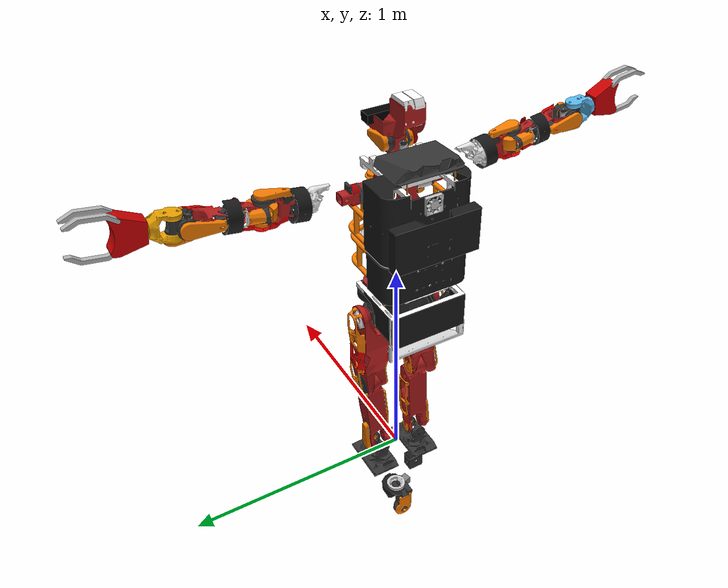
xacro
<?xml version="1.0"?>
<robot name="cart_humanoid" xmlns:xacro="http://ros.org/wiki/xacro" xmlns:xi="http://www.w3.org/2001/XInclude">
  <xacro:arg name="fix_base_link" default="false"/>
  <xacro:arg name="controllers_config" default=""/>

  <xacro:if value="$(arg fix_base_link)">
    <xacro:property name="base_link_joint_type" value="fixed" />
  </xacro:if>
  <xacro:unless value="$(arg fix_base_link)">
    <xacro:property name="base_link_joint_type" value="prismatic" />
  </xacro:unless>

  <!-- Include JAXON_RED robot URDF (contains links and joints) -->
  <xacro:include filename="$(find cart_humanoid_ros2)/urdf/JAXON_RED_gz.urdf.xacro" />

  <link name="world"/>
  <joint name="slide_x" type="${base_link_joint_type}">
    <parent link="world"/>
    <child link="slide_y_link"/>
    <limit effort="1000.0" lower="-999" upper="999" velocity="1"/>
    <axis xyz="1 0 0"/>
    <origin xyz="0 0 0.95" rpy="0 0 0" />
  </joint>

  <link name="slide_y_link">
    <inertial>
      <origin xyz="0 0 0"/>
      <mass value="1.0"/>
      <inertia ixx="1.0" ixy="0.0" ixz="0.0" iyy="1.0" iyz="0.0" izz="1.0" />
    </inertial>
  </link>

  <joint name="slide_y" type="${base_link_joint_type}">
    <parent link="slide_y_link"/>
    <child link="BODY"/>
    <limit effort="1000.0" lower="-999" upper="999" velocity="1"/>
    <axis xyz="0 1 0"/>
    <origin xyz="0 0 0" rpy="0 0 0" />
  </joint>

  <!-- Gazebo ROS2 Control Plugin -->
  <gazebo>
    <plugin filename="gz_ros2_control-system" name="gz_ros2_control::GazeboSimROS2ControlPlugin">
      <parameters>$(arg controllers_config)</parameters>
    </plugin>
  </gazebo>

</robot>

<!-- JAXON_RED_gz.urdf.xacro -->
<robot xmlns:xacro="http://www.ros.org/wiki/xacro" name="JAXON_RED">
  <!-- Include JAXON_RED body links and joints -->
  <xacro:include filename="JAXON_RED_body_stable_inertia.urdf" />

  <!-- ROS2 Control Hardware Interface -->
  <ros2_control name="GazeboSimSystem" type="system">
    <hardware>
      <plugin>gz_ros2_control/GazeboSimSystem</plugin>
    </hardware>

    <joint name="LLEG_JOINT0">
      <command_interface name="position"/>
      <state_interface name="position"/>
      <state_interface name="velocity"/>
    </joint>
    <joint name="LLEG_JOINT1">
      <command_interface name="position"/>
      <state_interface name="position"/>
      <state_interface name="velocity"/>
    </joint>
    <joint name="LLEG_JOINT2">
      <command_interface name="position"/>
      <state_interface name="position"/>
      <state_interface name="velocity"/>
    </joint>
    <joint name="LLEG_JOINT3">
      <command_interface name="position"/>
      <state_interface name="position"/>
      <state_interface name="velocity"/>
    </joint>
    <joint name="LLEG_JOINT4">
      <command_interface name="position"/>
      <state_interface name="position"/>
      <state_interface name="velocity"/>
    </joint>
    <joint name="LLEG_JOINT5">
      <command_interface name="position"/>
      <state_interface name="position"/>
      <state_interface name="velocity"/>
    </joint>

    <joint name="RLEG_JOINT0">
      <command_interface name="position"/>
      <state_interface name="position"/>
      <state_interface name="velocity"/>
    </joint>
    <joint name="RLEG_JOINT1">
      <command_interface name="position"/>
      <state_interface name="position"/>
      <state_interface name="velocity"/>
    </joint>
    <joint name="RLEG_JOINT2">
      <command_interface name="position"/>
      <state_interface name="position"/>
      <state_interface name="velocity"/>
    </joint>
    <joint name="RLEG_JOINT3">
      <command_interface name="position"/>
      <state_interface name="position"/>
      <state_interface name="velocity"/>
    </joint>
    <joint name="RLEG_JOINT4">
      <command_interface name="position"/>
      <state_interface name="position"/>
      <state_interface name="velocity"/>
    </joint>
    <joint name="RLEG_JOINT5">
      <command_interface name="position"/>
      <state_interface name="position"/>
      <state_interface name="velocity"/>
    </joint>

    <joint name="LARM_JOINT0">
      <command_interface name="position"/>
      <state_interface name="position"/>
      <state_interface name="velocity"/>
    </joint>
    <joint name="LARM_JOINT1">
      <command_interface name="position"/>
      <state_interface name="position"/>
      <state_interface name="velocity"/>
    </joint>
    <joint name="LARM_JOINT2">
      <command_interface name="position"/>
      <state_interface name="position"/>
      <state_interface name="velocity"/>
    </joint>
    <joint name="LARM_JOINT3">
      <command_interface name="position"/>
      <state_interface name="position"/>
      <state_interface name="velocity"/>
    </joint>
    <joint name="LARM_JOINT4">
      <command_interface name="position"/>
      <state_interface name="position"/>
      <state_interface name="velocity"/>
    </joint>
    <joint name="LARM_JOINT5">
      <command_interface name="position"/>
      <state_interface name="position"/>
      <state_interface name="velocity"/>
    </joint>
    <joint name="LARM_JOINT6">
      <command_interface name="position"/>
      <state_interface name="position"/>
      <state_interface name="velocity"/>
    </joint>
    <joint name="LARM_JOINT7">
      <command_interface name="position"/>
      <state_interface name="position"/>
      <state_interface name="velocity"/>
    </joint>

    <joint name="RARM_JOINT0">
      <command_interface name="position"/>
      <state_interface name="position"/>
      <state_interface name="velocity"/>
    </joint>
    <joint name="RARM_JOINT1">
      <command_interface name="position"/>
      <state_interface name="position"/>
      <state_interface name="velocity"/>
    </joint>
    <joint name="RARM_JOINT2">
      <command_interface name="position"/>
      <state_interface name="position"/>
      <state_interface name="velocity"/>
    </joint>
    <joint name="RARM_JOINT3">
      <command_interface name="position"/>
      <state_interface name="position"/>
      <state_interface name="velocity"/>
    </joint>
    <joint name="RARM_JOINT4">
      <command_interface name="position"/>
      <state_interface name="position"/>
      <state_interface name="velocity"/>
    </joint>
    <joint name="RARM_JOINT5">
      <command_interface name="position"/>
      <state_interface name="position"/>
      <state_interface name="velocity"/>
    </joint>
    <joint name="RARM_JOINT6">
      <command_interface name="position"/>
      <state_interface name="position"/>
      <state_interface name="velocity"/>
    </joint>
    <joint name="RARM_JOINT7">
      <command_interface name="position"/>
      <state_interface name="position"/>
      <state_interface name="velocity"/>
    </joint>

    <joint name="CHEST_JOINT0">
      <command_interface name="position"/>
      <state_interface name="position"/>
      <state_interface name="velocity"/>
    </joint>
    <joint name="CHEST_JOINT1">
      <command_interface name="position"/>
      <state_interface name="position"/>
      <state_interface name="velocity"/>
    </joint>
    <joint name="CHEST_JOINT2">
      <command_interface name="position"/>
      <state_interface name="position"/>
      <state_interface name="velocity"/>
    </joint>

    <joint name="HEAD_JOINT0">
      <command_interface name="position"/>
      <state_interface name="position"/>
      <state_interface name="velocity"/>
    </joint>
    <joint name="HEAD_JOINT1">
      <command_interface name="position"/>
      <state_interface name="position"/>
      <state_interface name="velocity"/>
    </joint>

    <joint name="L_finger1_joint">
      <command_interface name="position"/>
      <state_interface name="position"/>
      <state_interface name="velocity"/>
    </joint>

    <joint name="R_finger1_joint">
      <command_interface name="position"/>
      <state_interface name="position"/>
      <state_interface name="velocity"/>
    </joint>
  </ros2_control>

  <link name="LARM_LINK7">
    <visual>
      <origin xyz="0 0.0 0" rpy="0 -0 0"/>
      <geometry>
        <mesh filename="package://cart_humanoid_ros2/urdf/JAXON_RED_meshes/l_hand_attached_link.dae" scale="1 1 1" />
      </geometry>
    </visual>
    <collision>
      <origin xyz="0 0.12 0" rpy="0 -0 0"/>
      <geometry>
        <box size="0.1 0.25 0.1"/>
      </geometry>
    </collision>
    <inertial>
      <mass value="4.219" />
      <origin xyz="-0.02359 0.12884 -0.02825" rpy="0 -0 0"/>
      <inertia ixx="0.0527968" ixy="0" ixz="0" iyy="0.057042" iyz="0" izz="0.0492541"/>
    </inertial>
  </link>
  <gazebo reference="LARM_LINK7">
    <mu1>0.9</mu1>
    <mu2>0.9</mu2>
  </gazebo>

  <link name="RARM_LINK7">
    <visual>
      <origin xyz="0 0 0" rpy="0 -0 0"/>
      <geometry>
        <mesh filename="package://cart_humanoid_ros2/urdf/JAXON_RED_meshes/r_hand_attached_link.dae" scale="1 1 1" />
      </geometry>
    </visual>
    <collision>
      <origin xyz="0 -0.12 0" rpy="0 -0 0"/>
      <geometry>
        <box size="0.1 0.25 0.1"/>
      </geometry>
    </collision>
    <inertial>
      <mass value="4.219" />
      <origin xyz="0.02359 -0.12884 -0.02825" rpy="0 -0 0"/>
      <inertia ixx="0.0527968" ixy="0" ixz="0" iyy="0.057042" iyz="0" izz="0.0492541"/>
    </inertial>
  </link>
  <gazebo reference="RARM_LINK7">
    <mu1>0.9</mu1>
    <mu2>0.9</mu2>
  </gazebo>

  <!-- HEAD with camera sensor -->
  <joint name="adjuster_joint" type="fixed">
    <origin xyz="0.2 0 -0.2" rpy="0 0 0" />
    <parent link="HEAD_LINK1" />
    <child link="adjuster_link" />
  </joint>
  <link name="adjuster_link"/>

  <!-- Camera RGB frame (matching turtlebot kinect.urdf.xacro) -->
  <joint name="camera_rgb_joint" type="fixed">
    <origin xyz="-0.087 -0.0125 0.2870" rpy="0 0 0"/>
    <parent link="adjuster_link"/>
    <child link="camera_rgb_frame"/>
  </joint>
  <link name="camera_rgb_frame"/>

  <!-- Camera link and sensor -->
  <joint name="camera_joint" type="fixed">
    <origin xyz="-0.031 0.0125 -0.016" rpy="0 0 0"/>
    <parent link="camera_rgb_frame"/>
    <child link="camera_link"/>
  </joint>

  <link name="camera_link">
    <visual>
      <geometry>
        <box size="0.05 0.18 0.035"/>
      </geometry>
      <material name="kinect_color">
        <color rgba="0.0 0.0 0.0 1.0"/>
      </material>
    </visual>
    <collision>
      <geometry>
        <box size="0.05 0.18 0.035"/>
      </geometry>
    </collision>
    <inertial>
      <mass value="0.1"/>
      <origin xyz="0 0 0"/>
      <inertia ixx="0.001" ixy="0.0" ixz="0.0" iyy="0.001" iyz="0.0" izz="0.001"/>
    </inertial>
  </link>

  <!-- Camera depth frame (matching turtlebot kinect.urdf.xacro) -->
  <joint name="camera_depth_joint" type="fixed">
    <origin xyz="0 0.025 0" rpy="0 0 0"/>
    <parent link="camera_rgb_frame"/>
    <child link="camera_depth_frame"/>
  </joint>

  <link name="camera_depth_frame"/>

  <!-- Camera depth optical frame -->
  <joint name="camera_depth_optical_joint" type="fixed">
    <origin xyz="0 0 0" rpy="-1.5707963267948966 0 -1.5707963267948966"/>
    <parent link="camera_depth_frame"/>
    <child link="camera_depth_optical_frame"/>
  </joint>

  <link name="camera_depth_optical_frame"/>

  <!-- Gazebo Camera Sensor -->
  <gazebo reference="camera_link">
    <visual>
      <cast_shadows>false</cast_shadows>
    </visual>
    <sensor name="camera" type="rgbd_camera">
      <always_on>1</always_on>
      <update_rate>5</update_rate>
      <visualize>true</visualize>
      <topic>camera</topic>
      <gz_frame_id>camera_depth_optical_frame</gz_frame_id>
      <camera name="camera">
        <horizontal_fov>1.047198</horizontal_fov>
        <image>
          <width>320</width>
          <height>240</height>
          <format>R8G8B8</format>
        </image>
        <clip>
          <near>0.02</near>
          <far>8.0</far>
        </clip>
        <noise>
          <type>gaussian</type>
          <mean>0.0</mean>
          <stddev>0.007</stddev>
        </noise>
      </camera>
    </sensor>
  </gazebo>

  <!-- HAND -->
  <xacro:include filename="$(find cart_humanoid_ros2)/urdf/hand.urdf.xacro" />
  <xacro:jvrc_hand prefix="L_" parent="LARM_LINK7" type="revolute">
    <origin xyz="0 0 -0.085" rpy="3.141592654 1.5707963268 0" />
  </xacro:jvrc_hand>
  <xacro:jvrc_hand prefix="R_" parent="RARM_LINK7" type="revolute">
    <origin xyz="0 0 -0.085" rpy="0 1.5707963268 0" />
  </xacro:jvrc_hand>

</robot>

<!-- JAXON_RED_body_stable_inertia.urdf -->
<robot name="JAXON_RED" xmlns:xi="http://www.w3.org/2001/XInclude">

	<link name="BODY">

		<visual>

			<origin rpy="0 -0 0" xyz="0 0 1.0185"/>

			<geometry>

				<mesh filename="package://cart_humanoid_ros2/urdf/JAXON_RED_meshes/BODY_mesh.dae" scale="1 1 1"/>

			</geometry>

		</visual>

		<collision>

			<origin rpy="0 -0 0" xyz="0 0 1.0185"/>

			<geometry>

				<mesh filename="package://cart_humanoid_ros2/urdf/JAXON_RED_meshes/BODY_mesh.dae" scale="1 1 1"/>

			</geometry>

		</collision>

		<inertial>

			<mass value="22.7"/>

			<origin rpy="0 -0 0" xyz="-0.1059 -0.00067 -0.023"/>

			<inertia ixx="0.229835" ixy="0.00171" ixz="0.135708" iyy="0.535336" iyz="0.000616" izz="0.549159"/>

		</inertial>

	</link>

	<gazebo reference="BODY">

		<mu1>0.9</mu1>

		<mu2>0.9</mu2>

	</gazebo>

	<link name="CHEST_LINK0">

		<visual>

			<origin rpy="0 -0 0" xyz="0.006 0 0.128"/>

			<geometry>

				<mesh filename="package://cart_humanoid_ros2/urdf/JAXON_RED_meshes/CHEST_LINK0_mesh.dae" scale="1 1 1"/>

			</geometry>

		</visual>

		<collision>

			<origin rpy="0 -0 0" xyz="0.006 0 0.128"/>

			<geometry>

				<mesh filename="package://cart_humanoid_ros2/urdf/JAXON_RED_meshes/CHEST_LINK0_mesh.dae" scale="1 1 1"/>

			</geometry>

		</collision>

		<inertial>

			<mass value="0.866"/>

			<origin rpy="0 -0 0" xyz="-0.0084 0.00137 0.01359"/>

			<inertia ixx="0.00125384" ixy="0" ixz="0" iyy="0.00123407" iyz="0" izz="0.000677392"/>

		</inertial>

	</link>

	<gazebo reference="CHEST_LINK0">

		<mu1>0.9</mu1>

		<mu2>0.9</mu2>

	</gazebo>

	<link name="CHEST_LINK1">

		<visual>

			<origin rpy="0 -0 0" xyz="0 0 0.025"/>

			<geometry>

				<mesh filename="package://cart_humanoid_ros2/urdf/JAXON_RED_meshes/CHEST_LINK1_mesh.dae" scale="1 1 1"/>

			</geometry>

		</visual>

		<collision>

			<origin rpy="0 -0 0" xyz="0 0 0.025"/>

			<geometry>

				<mesh filename="package://cart_humanoid_ros2/urdf/JAXON_RED_meshes/CHEST_LINK1_mesh.dae" scale="1 1 1"/>

			</geometry>

		</collision>

		<inertial>

			<mass value="18.23"/>

			<origin rpy="0 -0 0" xyz="-0.111697 0.0039 0.03652"/>

			<inertia ixx="0.186526" ixy="0.003889" ixz="-0.039414" iyy="0.418012" iyz="0.001281" izz="0.477668"/>

		</inertial>

	</link>

	<gazebo reference="CHEST_LINK1">

		<mu1>0.9</mu1>

		<mu2>0.9</mu2>

	</gazebo>

	<link name="CHEST_LINK2">

		<visual>

			<origin rpy="0 -0 0" xyz="0 0 0.3085"/>

			<geometry>

				<mesh filename="package://cart_humanoid_ros2/urdf/JAXON_RED_meshes/CHEST_LINK2_mesh.dae" scale="1 1 1"/>

			</geometry>

		</visual>

		<collision>

			<origin rpy="0 -0 0" xyz="0 0 0.3085"/>

			<geometry>

				<mesh filename="package://cart_humanoid_ros2/urdf/JAXON_RED_meshes/CHEST_LINK2_mesh.dae" scale="1 1 1"/>

			</geometry>

		</collision>

		<inertial>

			<mass value="31.33"/>

			<origin rpy="0 -0 0" xyz="-0.13693 -0.00113 -0.05796"/>

			<inertia ixx="0.510746" ixy="0.005161" ixz="0.143334" iyy="1.09582" iyz="0.004687" izz="1.02505"/>

		</inertial>

	</link>

	<gazebo reference="CHEST_LINK2">

		<mu1>0.9</mu1>

		<mu2>0.9</mu2>

	</gazebo>

	<link name="HEAD_LINK0">

		<visual>

			<origin rpy="0 -0 0" xyz="-0.015 0 0.0835"/>

			<geometry>

				<mesh filename="package://cart_humanoid_ros2/urdf/JAXON_RED_meshes/HEAD_LINK0_mesh.dae" scale="1 1 1"/>

			</geometry>

		</visual>

		<collision>

			<origin rpy="0 -0 0" xyz="-0.015 0 0.0835"/>

			<geometry>

				<mesh filename="package://cart_humanoid_ros2/urdf/JAXON_RED_meshes/HEAD_LINK0_mesh.dae" scale="1 1 1"/>

			</geometry>

		</collision>

		<inertial>

			<mass value="1.086"/>

			<origin rpy="0 -0 0" xyz="-0.01227 3e-05 0.03231"/>

			<inertia ixx="0.1" ixy="0" ixz="0" iyy="0.1" iyz="0" izz="0.1"/>

		</inertial>

	</link>

	<gazebo reference="HEAD_LINK0">

		<mu1>0.9</mu1>

		<mu2>0.9</mu2>

	</gazebo>

	<link name="HEAD_LINK1">

		<visual>

			<origin rpy="0 -0 0" xyz="0 0 0.102"/>

			<geometry>

				<mesh filename="package://cart_humanoid_ros2/urdf/JAXON_RED_meshes/HEAD_LINK1_mesh.dae" scale="1 1 1"/>

			</geometry>

		</visual>

		<collision>

			<origin rpy="0 -0 0" xyz="0 0 0.102"/>

			<geometry>

				<mesh filename="package://cart_humanoid_ros2/urdf/JAXON_RED_meshes/HEAD_LINK1_mesh.dae" scale="1 1 1"/>

			</geometry>

		</collision>

		<inertial>

			<mass value="4.274"/>

			<origin rpy="0 -0 0" xyz="0.042 0.004 0.058"/>

			<inertia ixx="0.1" ixy="0" ixz="0" iyy="0.1" iyz="0" izz="0.1"/>

		</inertial>

	</link>

	<gazebo reference="HEAD_LINK1">

		<mu1>0.9</mu1>

		<mu2>0.9</mu2>

	</gazebo>

	<link name="LARM_LINK0">

		<visual>

			<origin rpy="0 -0 0" xyz="0 0.0875 0"/>

			<geometry>

				<mesh filename="package://cart_humanoid_ros2/urdf/JAXON_RED_meshes/LARM_LINK0_mesh.dae" scale="1 1 1"/>

			</geometry>

		</visual>

		<collision>

			<origin rpy="0 -0 0" xyz="0 0.0875 0"/>

			<geometry>

				<mesh filename="package://cart_humanoid_ros2/urdf/JAXON_RED_meshes/LARM_LINK0_mesh.dae" scale="1 1 1"/>

			</geometry>

		</collision>

		<inertial>

			<mass value="1.048"/>

			<origin rpy="0 -0 0" xyz="-0.01745 0.00887 -0.00015"/>

			<inertia ixx="0.1" ixy="0" ixz="0" iyy="0.1" iyz="0" izz="0.1"/>

		</inertial>

	</link>

	<gazebo reference="LARM_LINK0">

		<mu1>0.9</mu1>

		<mu2>0.9</mu2>

	</gazebo>

	<link name="LARM_LINK1">

		<visual>

			<origin rpy="0 -0 0" xyz="0 0.07275 0"/>

			<geometry>

				<mesh filename="package://cart_humanoid_ros2/urdf/JAXON_RED_meshes/LARM_LINK1_mesh.dae" scale="1 1 1"/>

			</geometry>

		</visual>

		<collision>

			<origin rpy="0 -0 0" xyz="0 0.07275 0"/>

			<geometry>

				<mesh filename="package://cart_humanoid_ros2/urdf/JAXON_RED_meshes/LARM_LINK1_mesh.dae" scale="1 1 1"/>

			</geometry>

		</collision>

		<inertial>

			<mass value="0.298"/>

			<origin rpy="0 -0 0" xyz="0.00011 0.01799 0.00288"/>

			<inertia ixx="0.1" ixy="0" ixz="0" iyy="0.1" iyz="0" izz="0.1"/>

		</inertial>

	</link>

	<gazebo reference="LARM_LINK1">

		<mu1>0.9</mu1>

		<mu2>0.9</mu2>

	</gazebo>

	<link name="LARM_LINK2">

		<visual>

			<origin rpy="0 -0 0" xyz="0 0.057 0"/>

			<geometry>

				<mesh filename="package://cart_humanoid_ros2/urdf/JAXON_RED_meshes/LARM_LINK2_mesh.dae" scale="1 1 1"/>

			</geometry>

		</visual>

		<collision>

			<origin rpy="0 -0 0" xyz="0 0.057 0"/>

			<geometry>

				<mesh filename="package://cart_humanoid_ros2/urdf/JAXON_RED_meshes/LARM_LINK2_mesh.dae" scale="1 1 1"/>

			</geometry>

		</collision>

		<inertial>

			<mass value="2.168"/>

			<origin rpy="0 -0 0" xyz="0.00845 0.00671 -0.0881"/>

			<inertia ixx="0.1" ixy="0" ixz="0" iyy="0.1" iyz="0" izz="0.1"/>

		</inertial>

	</link>

	<gazebo reference="LARM_LINK2">

		<mu1>0.9</mu1>

		<mu2>0.9</mu2>

	</gazebo>

	<link name="LARM_LINK3">

		<visual>

			<origin rpy="0 -0 0" xyz="0 0 -0.1965"/>

			<geometry>

				<mesh filename="package://cart_humanoid_ros2/urdf/JAXON_RED_meshes/LARM_LINK3_mesh.dae" scale="1 1 1"/>

			</geometry>

		</visual>

		<collision>

			<origin rpy="0 -0 0" xyz="0 0 -0.1965"/>

			<geometry>

				<mesh filename="package://cart_humanoid_ros2/urdf/JAXON_RED_meshes/LARM_LINK3_mesh.dae" scale="1 1 1"/>

			</geometry>

		</collision>

		<inertial>

			<mass value="1.315"/>

			<origin rpy="0 -0 0" xyz="0.01393 4e-05 -0.07574"/>

			<inertia ixx="0.1" ixy="0" ixz="0" iyy="0.1" iyz="0" izz="0.1"/>

		</inertial>

	</link>

	<gazebo reference="LARM_LINK3">

		<mu1>0.9</mu1>

		<mu2>0.9</mu2>

	</gazebo>

	<link name="LARM_LINK4">

		<visual>

			<origin rpy="0 -0 0" xyz="0 0 -0.126"/>

			<geometry>

				<mesh filename="package://cart_humanoid_ros2/urdf/JAXON_RED_meshes/LARM_LINK4_mesh.dae" scale="1 1 1"/>

			</geometry>

		</visual>

		<collision>

			<origin rpy="0 -0 0" xyz="0 0 -0.126"/>

			<geometry>

				<mesh filename="package://cart_humanoid_ros2/urdf/JAXON_RED_meshes/LARM_LINK4_mesh.dae" scale="1 1 1"/>

			</geometry>

		</collision>

		<inertial>

			<mass value="1.641"/>

			<origin rpy="0 -0 0" xyz="3e-05 0.00551 -0.0426"/>

			<inertia ixx="0.1" ixy="0" ixz="0" iyy="0.1" iyz="0" izz="0.1"/>

		</inertial>

	</link>

	<gazebo reference="LARM_LINK4">

		<mu1>0.9</mu1>

		<mu2>0.9</mu2>

	</gazebo>

	<link name="LARM_LINK5">

		<visual>

			<origin rpy="0 -0 0" xyz="0 0 -0.1275"/>

			<geometry>

				<mesh filename="package://cart_humanoid_ros2/urdf/JAXON_RED_meshes/LARM_LINK5_mesh.dae" scale="1 1 1"/>

			</geometry>

		</visual>

		<collision>

			<origin rpy="0 -0 0" xyz="0 0 -0.1275"/>

			<geometry>

				<mesh filename="package://cart_humanoid_ros2/urdf/JAXON_RED_meshes/LARM_LINK5_mesh.dae" scale="1 1 1"/>

			</geometry>

		</collision>

		<inertial>

			<mass value="1.305"/>

			<origin rpy="0 -0 0" xyz="0.01271 2e-05 -0.08415"/>

			<inertia ixx="0.1" ixy="0" ixz="0" iyy="0.1" iyz="0" izz="0.1"/>

		</inertial>

	</link>

	<gazebo reference="LARM_LINK5">

		<mu1>0.9</mu1>

		<mu2>0.9</mu2>

	</gazebo>

	<link name="LARM_LINK6">

		<visual>

			<origin rpy="0 -0 0" xyz="0 0 -0.146"/>

			<geometry>

				<mesh filename="package://cart_humanoid_ros2/urdf/JAXON_RED_meshes/LARM_LINK6_mesh.dae" scale="1 1 1"/>

			</geometry>

		</visual>

		<collision>

			<origin rpy="0 -0 0" xyz="0 0 -0.146"/>

			<geometry>

				<mesh filename="package://cart_humanoid_ros2/urdf/JAXON_RED_meshes/LARM_LINK6_mesh.dae" scale="1 1 1"/>

			</geometry>

		</collision>

		<inertial>

			<mass value="0.505"/>

			<origin rpy="0 -0 0" xyz="0.00013 0.01427 0.00188"/>

			<inertia ixx="0.1" ixy="0" ixz="0" iyy="0.1" iyz="0" izz="0.1"/>

		</inertial>

	</link>

	<gazebo reference="LARM_LINK6">

		<mu1>0.9</mu1>

		<mu2>0.9</mu2>

	</gazebo>

	<link name="RARM_LINK0">

		<visual>

			<origin rpy="0 -0 0" xyz="0 -0.0875 0"/>

			<geometry>

				<mesh filename="package://cart_humanoid_ros2/urdf/JAXON_RED_meshes/RARM_LINK0_mesh.dae" scale="1 1 1"/>

			</geometry>

		</visual>

		<collision>

			<origin rpy="0 -0 0" xyz="0 -0.0875 0"/>

			<geometry>

				<mesh filename="package://cart_humanoid_ros2/urdf/JAXON_RED_meshes/RARM_LINK0_mesh.dae" scale="1 1 1"/>

			</geometry>

		</collision>

		<inertial>

			<mass value="1.048"/>

			<origin rpy="0 -0 0" xyz="-0.01745 -0.00887 -0.00015"/>

			<inertia ixx="0.1" ixy="0" ixz="0" iyy="0.1" iyz="0" izz="0.1"/>

		</inertial>

	</link>

	<gazebo reference="RARM_LINK0">

		<mu1>0.9</mu1>

		<mu2>0.9</mu2>

	</gazebo>

	<link name="RARM_LINK1">

		<visual>

			<origin rpy="0 -0 0" xyz="0 -0.07275 0"/>

			<geometry>

				<mesh filename="package://cart_humanoid_ros2/urdf/JAXON_RED_meshes/RARM_LINK1_mesh.dae" scale="1 1 1"/>

			</geometry>

		</visual>

		<collision>

			<origin rpy="0 -0 0" xyz="0 -0.07275 0"/>

			<geometry>

				<mesh filename="package://cart_humanoid_ros2/urdf/JAXON_RED_meshes/RARM_LINK1_mesh.dae" scale="1 1 1"/>

			</geometry>

		</collision>

		<inertial>

			<mass value="0.298"/>

			<origin rpy="0 -0 0" xyz="0.00011 -0.01799 0.00288"/>

			<inertia ixx="0.1" ixy="0" ixz="0" iyy="0.1" iyz="0" izz="0.1"/>

		</inertial>

	</link>

	<gazebo reference="RARM_LINK1">

		<mu1>0.9</mu1>

		<mu2>0.9</mu2>

	</gazebo>

	<link name="RARM_LINK2">

		<visual>

			<origin rpy="0 -0 0" xyz="0 -0.057 0"/>

			<geometry>

				<mesh filename="package://cart_humanoid_ros2/urdf/JAXON_RED_meshes/RARM_LINK2_mesh.dae" scale="1 1 1"/>

			</geometry>

		</visual>

		<collision>

			<origin rpy="0 -0 0" xyz="0 -0.057 0"/>

			<geometry>

				<mesh filename="package://cart_humanoid_ros2/urdf/JAXON_RED_meshes/RARM_LINK2_mesh.dae" scale="1 1 1"/>

			</geometry>

		</collision>

		<inertial>

			<mass value="2.168"/>

			<origin rpy="0 -0 0" xyz="0.00845 -0.00671 -0.0881"/>

			<inertia ixx="0.1" ixy="0" ixz="0" iyy="0.1" iyz="0" izz="0.1"/>

		</inertial>

	</link>

	<gazebo reference="RARM_LINK2">

		<mu1>0.9</mu1>

		<mu2>0.9</mu2>

	</gazebo>

	<link name="RARM_LINK3">

		<visual>

			<origin rpy="0 -0 0" xyz="0 0 -0.1965"/>

			<geometry>

				<mesh filename="package://cart_humanoid_ros2/urdf/JAXON_RED_meshes/RARM_LINK3_mesh.dae" scale="1 1 1"/>

			</geometry>

		</visual>

		<collision>

			<origin rpy="0 -0 0" xyz="0 0 -0.1965"/>

			<geometry>

				<mesh filename="package://cart_humanoid_ros2/urdf/JAXON_RED_meshes/RARM_LINK3_mesh.dae" scale="1 1 1"/>

			</geometry>

		</collision>

		<inertial>

			<mass value="1.315"/>

			<origin rpy="0 -0 0" xyz="0.01393 -4e-05 -0.07574"/>

			<inertia ixx="0.1" ixy="0" ixz="0" iyy="0.1" iyz="0" izz="0.1"/>

		</inertial>

	</link>

	<gazebo reference="RARM_LINK3">

		<mu1>0.9</mu1>

		<mu2>0.9</mu2>

	</gazebo>

	<link name="RARM_LINK4">

		<visual>

			<origin rpy="0 -0 0" xyz="0 0 -0.126"/>

			<geometry>

				<mesh filename="package://cart_humanoid_ros2/urdf/JAXON_RED_meshes/RARM_LINK4_mesh.dae" scale="1 1 1"/>

			</geometry>

		</visual>

		<collision>

			<origin rpy="0 -0 0" xyz="0 0 -0.126"/>

			<geometry>

				<mesh filename="package://cart_humanoid_ros2/urdf/JAXON_RED_meshes/RARM_LINK4_mesh.dae" scale="1 1 1"/>

			</geometry>

		</collision>

		<inertial>

			<mass value="1.641"/>

			<origin rpy="0 -0 0" xyz="3e-05 -0.00551 -0.0426"/>

			<inertia ixx="0.1" ixy="0" ixz="0" iyy="0.1" iyz="0" izz="0.1"/>

		</inertial>

	</link>

	<gazebo reference="RARM_LINK4">

		<mu1>0.9</mu1>

		<mu2>0.9</mu2>

	</gazebo>

	<link name="RARM_LINK5">

		<visual>

			<origin rpy="0 -0 0" xyz="0 0 -0.1275"/>

			<geometry>

				<mesh filename="package://cart_humanoid_ros2/urdf/JAXON_RED_meshes/RARM_LINK5_mesh.dae" scale="1 1 1"/>

			</geometry>

		</visual>

		<collision>

			<origin rpy="0 -0 0" xyz="0 0 -0.1275"/>

			<geometry>

				<mesh filename="package://cart_humanoid_ros2/urdf/JAXON_RED_meshes/RARM_LINK5_mesh.dae" scale="1 1 1"/>

			</geometry>

		</collision>

		<inertial>

			<mass value="1.305"/>

			<origin rpy="0 -0 0" xyz="0.01271 -2e-05 -0.08415"/>

			<inertia ixx="0.1" ixy="0" ixz="0" iyy="0.1" iyz="0" izz="0.1"/>

		</inertial>

	</link>

	<gazebo reference="RARM_LINK5">

		<mu1>0.9</mu1>

		<mu2>0.9</mu2>

	</gazebo>

	<link name="RARM_LINK6">

		<visual>

			<origin rpy="0 -0 0" xyz="0 0 -0.146"/>

			<geometry>

				<mesh filename="package://cart_humanoid_ros2/urdf/JAXON_RED_meshes/RARM_LINK6_mesh.dae" scale="1 1 1"/>

			</geometry>

		</visual>

		<collision>

			<origin rpy="0 -0 0" xyz="0 0 -0.146"/>

			<geometry>

				<mesh filename="package://cart_humanoid_ros2/urdf/JAXON_RED_meshes/RARM_LINK6_mesh.dae" scale="1 1 1"/>

			</geometry>

		</collision>

		<inertial>

			<mass value="0.505"/>

			<origin rpy="0 -0 0" xyz="0.00013 -0.01427 0.00188"/>

			<inertia ixx="0.1" ixy="0" ixz="0" iyy="0.1" iyz="0" izz="0.1"/>

		</inertial>

	</link>

	<gazebo reference="RARM_LINK6">

		<mu1>0.9</mu1>

		<mu2>0.9</mu2>

	</gazebo>

	<link name="LLEG_LINK0">

		<visual>

			<origin rpy="0 -0 0" xyz="0 0.1 0.0095"/>

			<geometry>

				<mesh filename="package://cart_humanoid_ros2/urdf/JAXON_RED_meshes/LLEG_LINK0_mesh.dae" scale="1 1 1"/>

			</geometry>

		</visual>

		<collision>

			<origin rpy="0 -0 0" xyz="0 0.1 0.0095"/>

			<geometry>

				<mesh filename="package://cart_humanoid_ros2/urdf/JAXON_RED_meshes/LLEG_LINK0_mesh.dae" scale="1 1 1"/>

			</geometry>

		</collision>

		<inertial>

			<mass value="2.915"/>

			<origin rpy="0 -0 0" xyz="-0.02299 -0.00588 -0.07031"/>

			<inertia ixx="0.1" ixy="0" ixz="0" iyy="0.1" iyz="0" izz="0.1"/>

		</inertial>

	</link>

	<gazebo reference="LLEG_LINK0">

		<mu1>0.9</mu1>

		<mu2>0.9</mu2>

	</gazebo>

	<link name="LLEG_LINK1">

		<visual>

			<origin rpy="0 -0 0" xyz="0 0 -0.122"/>

			<geometry>

				<mesh filename="package://cart_humanoid_ros2/urdf/JAXON_RED_meshes/LLEG_LINK1_mesh.dae" scale="1 1 1"/>

			</geometry>

		</visual>

		<collision>

			<origin rpy="0 -0 0" xyz="0 0 -0.122"/>

			<geometry>

				<mesh filename="package://cart_humanoid_ros2/urdf/JAXON_RED_meshes/LLEG_LINK1_mesh.dae" scale="1 1 1"/>

			</geometry>

		</collision>

		<inertial>

			<mass value="1.199"/>

			<origin rpy="0 -0 0" xyz="-0.00441 0.00696 -0.00694"/>

			<inertia ixx="0.1" ixy="0" ixz="0" iyy="0.1" iyz="0" izz="0.1"/>

		</inertial>

	</link>

	<gazebo reference="LLEG_LINK1">

		<mu1>0.9</mu1>

		<mu2>0.9</mu2>

	</gazebo>

	<link name="LLEG_LINK2">

		<visual>

			<origin rpy="0 -0 0" xyz="0 0 -0.01"/>

			<geometry>

				<mesh filename="package://cart_humanoid_ros2/urdf/JAXON_RED_meshes/LLEG_LINK2_mesh.dae" scale="1 1 1"/>

			</geometry>

		</visual>

		<collision>

			<origin rpy="0 -0 0" xyz="0 0 -0.01"/>

			<geometry>

				<mesh filename="package://cart_humanoid_ros2/urdf/JAXON_RED_meshes/LLEG_LINK2_mesh.dae" scale="1 1 1"/>

			</geometry>

		</collision>

		<inertial>

			<mass value="5.783"/>

			<origin rpy="0 -0 0" xyz="0.00658 0.03431 -0.18864"/>

			<inertia ixx="0.1" ixy="0" ixz="0" iyy="0.1" iyz="0" izz="0.1"/>

		</inertial>

	</link>

	<gazebo reference="LLEG_LINK2">

		<mu1>0.9</mu1>

		<mu2>0.9</mu2>

	</gazebo>

	<link name="LLEG_LINK3">

		<visual>

			<origin rpy="0 -0 0" xyz="0 0 -0.38"/>

			<geometry>

				<mesh filename="package://cart_humanoid_ros2/urdf/JAXON_RED_meshes/LLEG_LINK3_mesh.dae" scale="1 1 1"/>

			</geometry>

		</visual>

		<collision>

			<origin rpy="0 -0 0" xyz="0 0 -0.38"/>

			<geometry>

				<mesh filename="package://cart_humanoid_ros2/urdf/JAXON_RED_meshes/LLEG_LINK3_mesh.dae" scale="1 1 1"/>

			</geometry>

		</collision>

		<inertial>

			<mass value="3.156"/>

			<origin rpy="0 -0 0" xyz="0.0176 0.01611 -0.17992"/>

			<inertia ixx="0.1" ixy="0" ixz="0" iyy="0.1" iyz="0" izz="0.1"/>

		</inertial>

	</link>

	<gazebo reference="LLEG_LINK3">

		<mu1>0.9</mu1>

		<mu2>0.9</mu2>

	</gazebo>

	<link name="LLEG_LINK4">

		<visual>

			<origin rpy="0 -0 0" xyz="0 0 -0.38"/>

			<geometry>

				<mesh filename="package://cart_humanoid_ros2/urdf/JAXON_RED_meshes/LLEG_LINK4_mesh.dae" scale="1 1 1"/>

			</geometry>

		</visual>

		<collision>

			<origin rpy="0 -0 0" xyz="0 0 -0.38"/>

			<geometry>

				<mesh filename="package://cart_humanoid_ros2/urdf/JAXON_RED_meshes/LLEG_LINK4_mesh.dae" scale="1 1 1"/>

			</geometry>

		</collision>

		<inertial>

			<mass value="0.836"/>

			<origin rpy="0 -0 0" xyz="-0.00769 0.00203 -0.00714"/>

			<inertia ixx="0.1" ixy="0" ixz="0" iyy="0.1" iyz="0" izz="0.1"/>

		</inertial>

	</link>

	<gazebo reference="LLEG_LINK4">

		<mu1>0.9</mu1>

		<mu2>0.9</mu2>

	</gazebo>

	<link name="LLEG_LINK5">

		<visual>

			<origin rpy="0 -0 0" xyz="0 0 -0.04"/>

			<geometry>

				<mesh filename="package://cart_humanoid_ros2/urdf/JAXON_RED_meshes/LLEG_LINK5_mesh.dae" scale="1 1 1"/>

			</geometry>

		</visual>

		<collision>

			<origin rpy="0 -0 0" xyz="0 0 -0.04"/>

			<geometry>

				<mesh filename="package://cart_humanoid_ros2/urdf/JAXON_RED_meshes/LLEG_LINK5_mesh.dae" scale="1 1 1"/>

			</geometry>

		</collision>

		<inertial>

			<mass value="1.552"/>

			<origin rpy="0 -0 0" xyz="0.00064 0.00264 -0.05633"/>

			<inertia ixx="0.1" ixy="0" ixz="0" iyy="0.1" iyz="0" izz="0.1"/>

		</inertial>

	</link>

	<gazebo reference="LLEG_LINK5">

		<mu1>0.9</mu1>

		<mu2>0.9</mu2>

	</gazebo>

	<link name="RLEG_LINK0">

		<visual>

			<origin rpy="0 -0 0" xyz="0 -0.1 0.0095"/>

			<geometry>

				<mesh filename="package://cart_humanoid_ros2/urdf/JAXON_RED_meshes/RLEG_LINK0_mesh.dae" scale="1 1 1"/>

			</geometry>

		</visual>

		<collision>

			<origin rpy="0 -0 0" xyz="0 -0.1 0.0095"/>

			<geometry>

				<mesh filename="package://cart_humanoid_ros2/urdf/JAXON_RED_meshes/RLEG_LINK0_mesh.dae" scale="1 1 1"/>

			</geometry>

		</collision>

		<inertial>

			<mass value="2.915"/>

			<origin rpy="0 -0 0" xyz="-0.02299 0.00588 -0.07031"/>

			<inertia ixx="0.1" ixy="0" ixz="0" iyy="0.1" iyz="0" izz="0.1"/>

		</inertial>

	</link>

	<gazebo reference="RLEG_LINK0">

		<mu1>0.9</mu1>

		<mu2>0.9</mu2>

	</gazebo>

	<link name="RLEG_LINK1">

		<visual>

			<origin rpy="0 -0 0" xyz="0 0 -0.122"/>

			<geometry>

				<mesh filename="package://cart_humanoid_ros2/urdf/JAXON_RED_meshes/RLEG_LINK1_mesh.dae" scale="1 1 1"/>

			</geometry>

		</visual>

		<collision>

			<origin rpy="0 -0 0" xyz="0 0 -0.122"/>

			<geometry>

				<mesh filename="package://cart_humanoid_ros2/urdf/JAXON_RED_meshes/RLEG_LINK1_mesh.dae" scale="1 1 1"/>

			</geometry>

		</collision>

		<inertial>

			<mass value="1.199"/>

			<origin rpy="0 -0 0" xyz="-0.00441 -0.00696 -0.00694"/>

			<inertia ixx="0.1" ixy="0" ixz="0" iyy="0.1" iyz="0" izz="0.1"/>

		</inertial>

	</link>

	<gazebo reference="RLEG_LINK1">

		<mu1>0.9</mu1>

		<mu2>0.9</mu2>

	</gazebo>

	<link name="RLEG_LINK2">

		<visual>

			<origin rpy="0 -0 0" xyz="0 0 -0.01"/>

			<geometry>

				<mesh filename="package://cart_humanoid_ros2/urdf/JAXON_RED_meshes/RLEG_LINK2_mesh.dae" scale="1 1 1"/>

			</geometry>

		</visual>

		<collision>

			<origin rpy="0 -0 0" xyz="0 0 -0.01"/>

			<geometry>

				<mesh filename="package://cart_humanoid_ros2/urdf/JAXON_RED_meshes/RLEG_LINK2_mesh.dae" scale="1 1 1"/>

			</geometry>

		</collision>

		<inertial>

			<mass value="5.783"/>

			<origin rpy="0 -0 0" xyz="0.00658 -0.03431 -0.18864"/>

			<inertia ixx="0.1" ixy="0" ixz="0" iyy="0.1" iyz="0" izz="0.1"/>

		</inertial>

	</link>

	<gazebo reference="RLEG_LINK2">

		<mu1>0.9</mu1>

		<mu2>0.9</mu2>

	</gazebo>

	<link name="RLEG_LINK3">

		<visual>

			<origin rpy="0 -0 0" xyz="0 0 -0.38"/>

			<geometry>

				<mesh filename="package://cart_humanoid_ros2/urdf/JAXON_RED_meshes/RLEG_LINK3_mesh.dae" scale="1 1 1"/>

			</geometry>

		</visual>

		<collision>

			<origin rpy="0 -0 0" xyz="0 0 -0.38"/>

			<geometry>

				<mesh filename="package://cart_humanoid_ros2/urdf/JAXON_RED_meshes/RLEG_LINK3_mesh.dae" scale="1 1 1"/>

			</geometry>

		</collision>

		<inertial>

			<mass value="3.156"/>

			<origin rpy="0 -0 0" xyz="0.0176 -0.01611 -0.17992"/>

			<inertia ixx="0.1" ixy="0" ixz="0" iyy="0.1" iyz="0" izz="0.1"/>

		</inertial>

	</link>

	<gazebo reference="RLEG_LINK3">

		<mu1>0.9</mu1>

		<mu2>0.9</mu2>

	</gazebo>

	<link name="RLEG_LINK4">

		<visual>

			<origin rpy="0 -0 0" xyz="0 0 -0.38"/>

			<geometry>

				<mesh filename="package://cart_humanoid_ros2/urdf/JAXON_RED_meshes/RLEG_LINK4_mesh.dae" scale="1 1 1"/>

			</geometry>

		</visual>

		<collision>

			<origin rpy="0 -0 0" xyz="0 0 -0.38"/>

			<geometry>

				<mesh filename="package://cart_humanoid_ros2/urdf/JAXON_RED_meshes/RLEG_LINK4_mesh.dae" scale="1 1 1"/>

			</geometry>

		</collision>

		<inertial>

			<mass value="0.836"/>

			<origin rpy="0 -0 0" xyz="-0.00769 -0.00203 -0.00714"/>

			<inertia ixx="0.1" ixy="0" ixz="0" iyy="0.1" iyz="0" izz="0.1"/>

		</inertial>

	</link>

	<gazebo reference="RLEG_LINK4">

		<mu1>0.9</mu1>

		<mu2>0.9</mu2>

	</gazebo>

	<link name="RLEG_LINK5">

		<visual>

			<origin rpy="0 -0 0" xyz="0 0 -0.04"/>

			<geometry>

				<mesh filename="package://cart_humanoid_ros2/urdf/JAXON_RED_meshes/RLEG_LINK5_mesh.dae" scale="1 1 1"/>

			</geometry>

		</visual>

		<collision>

			<origin rpy="0 -0 0" xyz="0 0 -0.04"/>

			<geometry>

				<mesh filename="package://cart_humanoid_ros2/urdf/JAXON_RED_meshes/RLEG_LINK5_mesh.dae" scale="1 1 1"/>

			</geometry>

		</collision>

		<inertial>

			<mass value="1.552"/>

			<origin rpy="0 -0 0" xyz="0.00064 -0.00264 -0.05633"/>

			<inertia ixx="0.1" ixy="0" ixz="0" iyy="0.1" iyz="0" izz="0.1"/>

		</inertial>

	</link>

	<gazebo reference="RLEG_LINK5">

		<mu1>0.9</mu1>

		<mu2>0.9</mu2>

	</gazebo>

	<joint name="CHEST_JOINT0" type="revolute">

		<parent link="BODY"/>

		<child link="CHEST_LINK0"/>

		<origin rpy="0 -0 0 " xyz="0.006 0 0.128"/>

		<axis xyz="1 0 0"/>

		<limit effort="869.069" lower="-0.198551" upper="0.198551" velocity="4"/>

		<dynamics damping="0.2" friction="0"/>

	</joint>

	<transmission name="CHEST_JOINT0_trans" type="pr2_mechanism_model/SimpleTransmission">

		<actuator name="CHEST_JOINT0_motor"/>

		<joint name="CHEST_JOINT0"/>

		<mechanicalReduction>1</mechanicalReduction>

	</transmission>

	<gazebo reference="CHEST_JOINT0">

		<cfmDamping>0.4</cfmDamping>

	</gazebo>

	<joint name="CHEST_JOINT1" type="revolute">

		<parent link="CHEST_LINK0"/>

		<child link="CHEST_LINK1"/>

		<origin rpy="0 -0 0 " xyz="0 0 0.025"/>

		<axis xyz="0 1 0"/>

		<limit effort="869.069" lower="-0.0349066" upper="0.610865" velocity="4"/>

		<dynamics damping="0.2" friction="0"/>

	</joint>

	<transmission name="CHEST_JOINT1_trans" type="pr2_mechanism_model/SimpleTransmission">

		<actuator name="CHEST_JOINT1_motor"/>

		<joint name="CHEST_JOINT1"/>

		<mechanicalReduction>1</mechanicalReduction>

	</transmission>

	<gazebo reference="CHEST_JOINT1">

		<cfmDamping>0.4</cfmDamping>

	</gazebo>

	<joint name="CHEST_JOINT2" type="revolute">

		<parent link="CHEST_LINK1"/>

		<child link="CHEST_LINK2"/>

		<origin rpy="0 -0 0 " xyz="0 0 0.3085"/>

		<axis xyz="0 0 1"/>

		<limit effort="434.534" lower="-1.0566" upper="1.0566" velocity="4"/>

		<dynamics damping="0.2" friction="0"/>

	</joint>

	<transmission name="CHEST_JOINT2_trans" type="pr2_mechanism_model/SimpleTransmission">

		<actuator name="CHEST_JOINT2_motor"/>

		<joint name="CHEST_JOINT2"/>

		<mechanicalReduction>1</mechanicalReduction>

	</transmission>

	<gazebo reference="CHEST_JOINT2">

		<cfmDamping>0.4</cfmDamping>

	</gazebo>

	<joint name="HEAD_JOINT0" type="revolute">

		<parent link="CHEST_LINK2"/>

		<child link="HEAD_LINK0"/>

		<origin rpy="0 -0 0 " xyz="-0.015 0 0.0835"/>

		<axis xyz="0 0 1"/>

		<limit effort="287.171" lower="-0.392699" upper="0.392699" velocity="4"/>

		<dynamics damping="0.2" friction="0"/>

	</joint>

	<transmission name="HEAD_JOINT0_trans" type="pr2_mechanism_model/SimpleTransmission">

		<actuator name="HEAD_JOINT0_motor"/>

		<joint name="HEAD_JOINT0"/>

		<mechanicalReduction>1</mechanicalReduction>

	</transmission>

	<gazebo reference="HEAD_JOINT0">

		<cfmDamping>0.4</cfmDamping>

	</gazebo>

	<joint name="HEAD_JOINT1" type="revolute">

		<parent link="HEAD_LINK0"/>

		<child link="HEAD_LINK1"/>

		<origin rpy="0 -0 0 " xyz="0 0 0.102"/>

		<axis xyz="0 1 0"/>

		<limit effort="287.171" lower="-0.549779" upper="0.671952" velocity="4"/>

		<dynamics damping="0.2" friction="0"/>

	</joint>

	<transmission name="HEAD_JOINT1_trans" type="pr2_mechanism_model/SimpleTransmission">

		<actuator name="HEAD_JOINT1_motor"/>

		<joint name="HEAD_JOINT1"/>

		<mechanicalReduction>1</mechanicalReduction>

	</transmission>

	<gazebo reference="HEAD_JOINT1">

		<cfmDamping>0.4</cfmDamping>

	</gazebo>

	<joint name="LARM_JOINT0" type="revolute">

		<parent link="CHEST_LINK2"/>

		<child link="LARM_LINK0"/>

		<origin rpy="0 -0 0 " xyz="0 0.0875 0"/>

		<axis xyz="0 0 1"/>

		<limit effort="287.171" lower="-1.4208" upper="0.144751" velocity="4"/>

		<dynamics damping="0.2" friction="0"/>

	</joint>

	<transmission name="LARM_JOINT0_trans" type="pr2_mechanism_model/SimpleTransmission">

		<actuator name="LARM_JOINT0_motor"/>

		<joint name="LARM_JOINT0"/>

		<mechanicalReduction>1</mechanicalReduction>

	</transmission>

	<gazebo reference="LARM_JOINT0">

		<cfmDamping>0.4</cfmDamping>

	</gazebo>

	<joint name="LARM_JOINT1" type="revolute">

		<parent link="LARM_LINK0"/>

		<child link="LARM_LINK1"/>

		<origin rpy="0 -0 0 " xyz="0 0.07275 0"/>

		<axis xyz="0 1 0"/>

		<limit effort="287.171" lower="-3.14159" upper="3.14159" velocity="4"/>

		<dynamics damping="0.2" friction="0"/>

	</joint>

	<transmission name="LARM_JOINT1_trans" type="pr2_mechanism_model/SimpleTransmission">

		<actuator name="LARM_JOINT1_motor"/>

		<joint name="LARM_JOINT1"/>

		<mechanicalReduction>1</mechanicalReduction>

	</transmission>

	<gazebo reference="LARM_JOINT1">

		<cfmDamping>0.4</cfmDamping>

	</gazebo>

	<joint name="LARM_JOINT2" type="revolute">

		<parent link="LARM_LINK1"/>

		<child link="LARM_LINK2"/>

		<origin rpy="0 -0 0 " xyz="0 0.057 0"/>

		<axis xyz="1 0 0"/>

		<limit effort="287.171" lower="0.2762" upper="3.14159" velocity="4"/>

		<dynamics damping="0.2" friction="0"/>

	</joint>

	<transmission name="LARM_JOINT2_trans" type="pr2_mechanism_model/SimpleTransmission">

		<actuator name="LARM_JOINT2_motor"/>

		<joint name="LARM_JOINT2"/>

		<mechanicalReduction>1</mechanicalReduction>

	</transmission>

	<gazebo reference="LARM_JOINT2">

		<cfmDamping>0.4</cfmDamping>

	</gazebo>

	<joint name="LARM_JOINT3" type="revolute">

		<parent link="LARM_LINK2"/>

		<child link="LARM_LINK3"/>

		<origin rpy="0 -0 0 " xyz="0 0 -0.1965"/>

		<axis xyz="0 0 1"/>

		<limit effort="287.171" lower="-3.14159" upper="3.14159" velocity="4"/>

		<dynamics damping="0.2" friction="0"/>

	</joint>

	<transmission name="LARM_JOINT3_trans" type="pr2_mechanism_model/SimpleTransmission">

		<actuator name="LARM_JOINT3_motor"/>

		<joint name="LARM_JOINT3"/>

		<mechanicalReduction>1</mechanicalReduction>

	</transmission>

	<gazebo reference="LARM_JOINT3">

		<cfmDamping>0.4</cfmDamping>

	</gazebo>

	<joint name="LARM_JOINT4" type="revolute">

		<parent link="LARM_LINK3"/>

		<child link="LARM_LINK4"/>

		<origin rpy="0 -0 0 " xyz="0 0 -0.126"/>

		<axis xyz="0 1 0"/>

		<limit effort="287.171" lower="-2.19006" upper="1.0472" velocity="4"/>

		<dynamics damping="0.2" friction="0"/>

	</joint>

	<transmission name="LARM_JOINT4_trans" type="pr2_mechanism_model/SimpleTransmission">

		<actuator name="LARM_JOINT4_motor"/>

		<joint name="LARM_JOINT4"/>

		<mechanicalReduction>1</mechanicalReduction>

	</transmission>

	<gazebo reference="LARM_JOINT4">

		<cfmDamping>0.4</cfmDamping>

	</gazebo>

	<joint name="LARM_JOINT5" type="revolute">

		<parent link="LARM_LINK4"/>

		<child link="LARM_LINK5"/>

		<origin rpy="0 -0 0 " xyz="0 0 -0.1275"/>

		<axis xyz="0 0 1"/>

		<limit effort="287.171" lower="-3.14159" upper="3.14159" velocity="4"/>

		<dynamics damping="0.2" friction="0"/>

	</joint>

	<transmission name="LARM_JOINT5_trans" type="pr2_mechanism_model/SimpleTransmission">

		<actuator name="LARM_JOINT5_motor"/>

		<joint name="LARM_JOINT5"/>

		<mechanicalReduction>1</mechanicalReduction>

	</transmission>

	<gazebo reference="LARM_JOINT5">

		<cfmDamping>0.4</cfmDamping>

	</gazebo>

	<joint name="LARM_JOINT6" type="revolute">

		<parent link="LARM_LINK5"/>

		<child link="LARM_LINK6"/>

		<origin rpy="0 -0 0 " xyz="0 0 -0.146"/>

		<axis xyz="1 0 0"/>

		<limit effort="287.171" lower="-1.54494" upper="1.5708" velocity="4"/>

		<dynamics damping="0.2" friction="0"/>

	</joint>

	<transmission name="LARM_JOINT6_trans" type="pr2_mechanism_model/SimpleTransmission">

		<actuator name="LARM_JOINT6_motor"/>

		<joint name="LARM_JOINT6"/>

		<mechanicalReduction>1</mechanicalReduction>

	</transmission>

	<gazebo reference="LARM_JOINT6">

		<cfmDamping>0.4</cfmDamping>

	</gazebo>

	<joint name="LARM_JOINT7" type="revolute">

		<parent link="LARM_LINK6"/>

		<child link="LARM_LINK7"/>

		<origin rpy="0 -0 0 " xyz="0 0 -0.04"/>

		<axis xyz="0 1 0"/>

		<limit effort="288.965" lower="-1.41372" upper="1.0472" velocity="4"/>

		<dynamics damping="0.2" friction="0"/>

	</joint>

	<transmission name="LARM_JOINT7_trans" type="pr2_mechanism_model/SimpleTransmission">

		<actuator name="LARM_JOINT7_motor"/>

		<joint name="LARM_JOINT7"/>

		<mechanicalReduction>1</mechanicalReduction>

	</transmission>

	<gazebo reference="LARM_JOINT7">

		<cfmDamping>0.4</cfmDamping>

	</gazebo>

	<joint name="RARM_JOINT0" type="revolute">

		<parent link="CHEST_LINK2"/>

		<child link="RARM_LINK0"/>

		<origin rpy="0 -0 0 " xyz="0 -0.0875 0"/>

		<axis xyz="0 0 1"/>

		<limit effort="287.171" lower="-0.144751" upper="1.4208" velocity="4"/>

		<dynamics damping="0.2" friction="0"/>

	</joint>

	<transmission name="RARM_JOINT0_trans" type="pr2_mechanism_model/SimpleTransmission">

		<actuator name="RARM_JOINT0_motor"/>

		<joint name="RARM_JOINT0"/>

		<mechanicalReduction>1</mechanicalReduction>

	</transmission>

	<gazebo reference="RARM_JOINT0">

		<cfmDamping>0.4</cfmDamping>

	</gazebo>

	<joint name="RARM_JOINT1" type="revolute">

		<parent link="RARM_LINK0"/>

		<child link="RARM_LINK1"/>

		<origin rpy="0 -0 0 " xyz="0 -0.07275 0"/>

		<axis xyz="0 1 0"/>

		<limit effort="287.171" lower="-3.14159" upper="3.14159" velocity="4"/>

		<dynamics damping="0.2" friction="0"/>

	</joint>

	<transmission name="RARM_JOINT1_trans" type="pr2_mechanism_model/SimpleTransmission">

		<actuator name="RARM_JOINT1_motor"/>

		<joint name="RARM_JOINT1"/>

		<mechanicalReduction>1</mechanicalReduction>

	</transmission>

	<gazebo reference="RARM_JOINT1">

		<cfmDamping>0.4</cfmDamping>

	</gazebo>

	<joint name="RARM_JOINT2" type="revolute">

		<parent link="RARM_LINK1"/>

		<child link="RARM_LINK2"/>

		<origin rpy="0 -0 0 " xyz="0 -0.057 0"/>

		<axis xyz="1 0 0"/>

		<limit effort="287.171" lower="-3.14159" upper="-0.2762" velocity="4"/>

		<dynamics damping="0.2" friction="0"/>

	</joint>

	<transmission name="RARM_JOINT2_trans" type="pr2_mechanism_model/SimpleTransmission">

		<actuator name="RARM_JOINT2_motor"/>

		<joint name="RARM_JOINT2"/>

		<mechanicalReduction>1</mechanicalReduction>

	</transmission>

	<gazebo reference="RARM_JOINT2">

		<cfmDamping>0.4</cfmDamping>

	</gazebo>

	<joint name="RARM_JOINT3" type="revolute">

		<parent link="RARM_LINK2"/>

		<child link="RARM_LINK3"/>

		<origin rpy="0 -0 0 " xyz="0 0 -0.1965"/>

		<axis xyz="0 0 1"/>

		<limit effort="287.171" lower="-3.14159" upper="3.14159" velocity="4"/>

		<dynamics damping="0.2" friction="0"/>

	</joint>

	<transmission name="RARM_JOINT3_trans" type="pr2_mechanism_model/SimpleTransmission">

		<actuator name="RARM_JOINT3_motor"/>

		<joint name="RARM_JOINT3"/>

		<mechanicalReduction>1</mechanicalReduction>

	</transmission>

	<gazebo reference="RARM_JOINT3">

		<cfmDamping>0.4</cfmDamping>

	</gazebo>

	<joint name="RARM_JOINT4" type="revolute">

		<parent link="RARM_LINK3"/>

		<child link="RARM_LINK4"/>

		<origin rpy="0 -0 0 " xyz="0 0 -0.126"/>

		<axis xyz="0 1 0"/>

		<limit effort="287.171" lower="-2.19006" upper="1.0472" velocity="4"/>

		<dynamics damping="0.2" friction="0"/>

	</joint>

	<transmission name="RARM_JOINT4_trans" type="pr2_mechanism_model/SimpleTransmission">

		<actuator name="RARM_JOINT4_motor"/>

		<joint name="RARM_JOINT4"/>

		<mechanicalReduction>1</mechanicalReduction>

	</transmission>

	<gazebo reference="RARM_JOINT4">

		<cfmDamping>0.4</cfmDamping>

	</gazebo>

	<joint name="RARM_JOINT5" type="revolute">

		<parent link="RARM_LINK4"/>

		<child link="RARM_LINK5"/>

		<origin rpy="0 -0 0 " xyz="0 0 -0.1275"/>

		<axis xyz="0 0 1"/>

		<limit effort="287.171" lower="-3.14159" upper="3.14159" velocity="4"/>

		<dynamics damping="0.2" friction="0"/>

	</joint>

	<transmission name="RARM_JOINT5_trans" type="pr2_mechanism_model/SimpleTransmission">

		<actuator name="RARM_JOINT5_motor"/>

		<joint name="RARM_JOINT5"/>

		<mechanicalReduction>1</mechanicalReduction>

	</transmission>

	<gazebo reference="RARM_JOINT5">

		<cfmDamping>0.4</cfmDamping>

	</gazebo>

	<joint name="RARM_JOINT6" type="revolute">

		<parent link="RARM_LINK5"/>

		<child link="RARM_LINK6"/>

		<origin rpy="0 -0 0 " xyz="0 0 -0.146"/>

		<axis xyz="1 0 0"/>

		<limit effort="287.171" lower="-1.5708" upper="1.54494" velocity="4"/>

		<dynamics damping="0.2" friction="0"/>

	</joint>

	<transmission name="RARM_JOINT6_trans" type="pr2_mechanism_model/SimpleTransmission">

		<actuator name="RARM_JOINT6_motor"/>

		<joint name="RARM_JOINT6"/>

		<mechanicalReduction>1</mechanicalReduction>

	</transmission>

	<gazebo reference="RARM_JOINT6">

		<cfmDamping>0.4</cfmDamping>

	</gazebo>

	<joint name="RARM_JOINT7" type="revolute">

		<parent link="RARM_LINK6"/>

		<child link="RARM_LINK7"/>

		<origin rpy="0 -0 0 " xyz="0 0 -0.04"/>

		<axis xyz="0 1 0"/>

		<limit effort="288.965" lower="-1.41372" upper="1.0472" velocity="4"/>

		<dynamics damping="0.2" friction="0"/>

	</joint>

	<transmission name="RARM_JOINT7_trans" type="pr2_mechanism_model/SimpleTransmission">

		<actuator name="RARM_JOINT7_motor"/>

		<joint name="RARM_JOINT7"/>

		<mechanicalReduction>1</mechanicalReduction>

	</transmission>

	<gazebo reference="RARM_JOINT7">

		<cfmDamping>0.4</cfmDamping>

	</gazebo>

	<joint name="LLEG_JOINT0" type="revolute">

		<parent link="BODY"/>

		<child link="LLEG_LINK0"/>

		<origin rpy="0 -0 0 " xyz="0 0.1 0.0095"/>

		<axis xyz="0 0 1"/>

		<limit effort="339.972" lower="-1.0972" upper="1.02662" velocity="9"/>

		<dynamics damping="0.2" friction="0"/>

	</joint>

	<transmission name="LLEG_JOINT0_trans" type="pr2_mechanism_model/SimpleTransmission">

		<actuator name="LLEG_JOINT0_motor"/>

		<joint name="LLEG_JOINT0"/>

		<mechanicalReduction>1</mechanicalReduction>

	</transmission>

	<gazebo reference="LLEG_JOINT0">

		<cfmDamping>0.4</cfmDamping>

	</gazebo>

	<joint name="LLEG_JOINT1" type="revolute">

		<parent link="LLEG_LINK0"/>

		<child link="LLEG_LINK1"/>

		<origin rpy="0 -0 0 " xyz="0 0 -0.122"/>

		<axis xyz="1 0 0"/>

		<limit effort="543.955" lower="-0.523599" upper="0.725029" velocity="9"/>

		<dynamics damping="0.2" friction="0"/>

	</joint>

	<transmission name="LLEG_JOINT1_trans" type="pr2_mechanism_model/SimpleTransmission">

		<actuator name="LLEG_JOINT1_motor"/>

		<joint name="LLEG_JOINT1"/>

		<mechanicalReduction>1</mechanicalReduction>

	</transmission>

	<gazebo reference="LLEG_JOINT1">

		<cfmDamping>0.4</cfmDamping>

	</gazebo>

	<joint name="LLEG_JOINT2" type="revolute">

		<parent link="LLEG_LINK1"/>

		<child link="LLEG_LINK2"/>

		<origin rpy="0 -0 0 " xyz="0 0 -0.01"/>

		<axis xyz="0 1 0"/>

		<limit effort="679.944" lower="-2.11843" upper="0.785398" velocity="9"/>

		<dynamics damping="0.2" friction="0"/>

	</joint>

	<transmission name="LLEG_JOINT2_trans" type="pr2_mechanism_model/SimpleTransmission">

		<actuator name="LLEG_JOINT2_motor"/>

		<joint name="LLEG_JOINT2"/>

		<mechanicalReduction>1</mechanicalReduction>

	</transmission>

	<gazebo reference="LLEG_JOINT2">

		<cfmDamping>0.4</cfmDamping>

	</gazebo>

	<joint name="LLEG_JOINT3" type="revolute">

		<parent link="LLEG_LINK2"/>

		<child link="LLEG_LINK3"/>

		<origin rpy="0 -0 0 " xyz="0 0 -0.38"/>

		<axis xyz="0 1 0"/>

		<limit effort="679.944" lower="0" upper="2.77419" velocity="9"/>

		<dynamics damping="0.2" friction="0"/>

	</joint>

	<transmission name="LLEG_JOINT3_trans" type="pr2_mechanism_model/SimpleTransmission">

		<actuator name="LLEG_JOINT3_motor"/>

		<joint name="LLEG_JOINT3"/>

		<mechanicalReduction>1</mechanicalReduction>

	</transmission>

	<gazebo reference="LLEG_JOINT3">

		<cfmDamping>0.4</cfmDamping>

	</gazebo>

	<joint name="LLEG_JOINT4" type="revolute">

		<parent link="LLEG_LINK3"/>

		<child link="LLEG_LINK4"/>

		<origin rpy="0 -0 0 " xyz="0 0 -0.38"/>

		<axis xyz="0 1 0"/>

		<limit effort="407.966" lower="-1.38564" upper="1.47343" velocity="9"/>

		<dynamics damping="0.2" friction="0"/>

	</joint>

	<transmission name="LLEG_JOINT4_trans" type="pr2_mechanism_model/SimpleTransmission">

		<actuator name="LLEG_JOINT4_motor"/>

		<joint name="LLEG_JOINT4"/>

		<mechanicalReduction>1</mechanicalReduction>

	</transmission>

	<gazebo reference="LLEG_JOINT4">

		<cfmDamping>0.4</cfmDamping>

	</gazebo>

	<joint name="LLEG_JOINT5" type="revolute">

		<parent link="LLEG_LINK4"/>

		<child link="LLEG_LINK5"/>

		<origin rpy="0 -0 0 " xyz="0 0 -0.04"/>

		<axis xyz="1 0 0"/>

		<limit effort="342.097" lower="-1.0472" upper="1.0472" velocity="9"/>

		<dynamics damping="0.2" friction="0"/>

	</joint>

	<transmission name="LLEG_JOINT5_trans" type="pr2_mechanism_model/SimpleTransmission">

		<actuator name="LLEG_JOINT5_motor"/>

		<joint name="LLEG_JOINT5"/>

		<mechanicalReduction>1</mechanicalReduction>

	</transmission>

	<gazebo reference="LLEG_JOINT5">

		<cfmDamping>0.4</cfmDamping>

	</gazebo>

	<joint name="RLEG_JOINT0" type="revolute">

		<parent link="BODY"/>

		<child link="RLEG_LINK0"/>

		<origin rpy="0 -0 0 " xyz="0 -0.1 0.0095"/>

		<axis xyz="0 0 1"/>

		<limit effort="339.972" lower="-1.02662" upper="1.0972" velocity="9"/>

		<dynamics damping="0.2" friction="0"/>

	</joint>

	<transmission name="RLEG_JOINT0_trans" type="pr2_mechanism_model/SimpleTransmission">

		<actuator name="RLEG_JOINT0_motor"/>

		<joint name="RLEG_JOINT0"/>

		<mechanicalReduction>1</mechanicalReduction>

	</transmission>

	<gazebo reference="RLEG_JOINT0">

		<cfmDamping>0.4</cfmDamping>

	</gazebo>

	<joint name="RLEG_JOINT1" type="revolute">

		<parent link="RLEG_LINK0"/>

		<child link="RLEG_LINK1"/>

		<origin rpy="0 -0 0 " xyz="0 0 -0.122"/>

		<axis xyz="1 0 0"/>

		<limit effort="543.955" lower="-0.725029" upper="0.523599" velocity="9"/>

		<dynamics damping="0.2" friction="0"/>

	</joint>

	<transmission name="RLEG_JOINT1_trans" type="pr2_mechanism_model/SimpleTransmission">

		<actuator name="RLEG_JOINT1_motor"/>

		<joint name="RLEG_JOINT1"/>

		<mechanicalReduction>1</mechanicalReduction>

	</transmission>

	<gazebo reference="RLEG_JOINT1">

		<cfmDamping>0.4</cfmDamping>

	</gazebo>

	<joint name="RLEG_JOINT2" type="revolute">

		<parent link="RLEG_LINK1"/>

		<child link="RLEG_LINK2"/>

		<origin rpy="0 -0 0 " xyz="0 0 -0.01"/>

		<axis xyz="0 1 0"/>

		<limit effort="679.944" lower="-2.11843" upper="0.785398" velocity="9"/>

		<dynamics damping="0.2" friction="0"/>

	</joint>

	<transmission name="RLEG_JOINT2_trans" type="pr2_mechanism_model/SimpleTransmission">

		<actuator name="RLEG_JOINT2_motor"/>

		<joint name="RLEG_JOINT2"/>

		<mechanicalReduction>1</mechanicalReduction>

	</transmission>

	<gazebo reference="RLEG_JOINT2">

		<cfmDamping>0.4</cfmDamping>

	</gazebo>

	<joint name="RLEG_JOINT3" type="revolute">

		<parent link="RLEG_LINK2"/>

		<child link="RLEG_LINK3"/>

		<origin rpy="0 -0 0 " xyz="0 0 -0.38"/>

		<axis xyz="0 1 0"/>

		<limit effort="679.944" lower="0" upper="2.77419" velocity="9"/>

		<dynamics damping="0.2" friction="0"/>

	</joint>

	<transmission name="RLEG_JOINT3_trans" type="pr2_mechanism_model/SimpleTransmission">

		<actuator name="RLEG_JOINT3_motor"/>

		<joint name="RLEG_JOINT3"/>

		<mechanicalReduction>1</mechanicalReduction>

	</transmission>

	<gazebo reference="RLEG_JOINT3">

		<cfmDamping>0.4</cfmDamping>

	</gazebo>

	<joint name="RLEG_JOINT4" type="revolute">

		<parent link="RLEG_LINK3"/>

		<child link="RLEG_LINK4"/>

		<origin rpy="0 -0 0 " xyz="0 0 -0.38"/>

		<axis xyz="0 1 0"/>

		<limit effort="407.966" lower="-1.38564" upper="1.47343" velocity="9"/>

		<dynamics damping="0.2" friction="0"/>

	</joint>

	<transmission name="RLEG_JOINT4_trans" type="pr2_mechanism_model/SimpleTransmission">

		<actuator name="RLEG_JOINT4_motor"/>

		<joint name="RLEG_JOINT4"/>

		<mechanicalReduction>1</mechanicalReduction>

	</transmission>

	<gazebo reference="RLEG_JOINT4">

		<cfmDamping>0.4</cfmDamping>

	</gazebo>

	<joint name="RLEG_JOINT5" type="revolute">

		<parent link="RLEG_LINK4"/>

		<child link="RLEG_LINK5"/>

		<origin rpy="0 -0 0 " xyz="0 0 -0.04"/>

		<axis xyz="1 0 0"/>

		<limit effort="342.097" lower="-1.0472" upper="1.0472" velocity="9"/>

		<dynamics damping="0.2" friction="0"/>

	</joint>

	<transmission name="RLEG_JOINT5_trans" type="pr2_mechanism_model/SimpleTransmission">

		<actuator name="RLEG_JOINT5_motor"/>

		<joint name="RLEG_JOINT5"/>

		<mechanicalReduction>1</mechanicalReduction>

	</transmission>

	<gazebo reference="RLEG_JOINT5">

		<cfmDamping>0.4</cfmDamping>

	</gazebo>

</robot>

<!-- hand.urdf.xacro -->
<robot xmlns:xacro="http://ros.org/wiki/xacro" name="JVRC_HAND">
  <!-- inertial parameter is not correct -->
  <xacro:macro name="jvrc_hand" params="prefix parent type *origin">
    <link name="${prefix}palm">
      <inertial>
        <origin xyz="0.0835 0 -0.0181" rpy="0 0 0" />
        <mass value="0.8" />
        <inertia ixx="0.001314416" ixy="0" ixz="0" iyy="0.002746271" iyz="0" izz="0.002284148"/>
      </inertial>
      <visual>
        <geometry>
          <mesh filename="package://cart_humanoid_ros2/urdf/hand_meshes/JVRC_palm.stl" />
        </geometry>
        <material name="red">
          <color rgba="0.8 0.0 0.0 1.0"/>
        </material>
      </visual>
      <collision>
        <geometry>
          <mesh filename="package://cart_humanoid_ros2/urdf/hand_meshes/JVRC_palm.stl" />
        </geometry>
      </collision>
    </link>

    <link name="${prefix}finger1">
      <inertial>
        <origin xyz="0.021 0 -0.04556" rpy="0 0 0" />
        <mass value="0.2" />
        <inertia ixx="0.1" ixy="0" ixz="0" iyy="0.1" iyz="0" izz="0.1"/>
      </inertial>
      <visual>
        <origin xyz="0.0 0 0" rpy="0 0 0" />
        <geometry>
          <mesh filename="package://cart_humanoid_ros2/urdf/hand_meshes/JVRC_finger1.stl" />
        </geometry>
        <material name="finger">
          <color rgba="0.7 0.7 0.7 1.0"/>
        </material>
      </visual>
      <collision>
        <origin xyz="0.0 0 0" rpy="0 0 0" />
        <geometry>
          <mesh filename="package://cart_humanoid_ros2/urdf/hand_meshes/JVRC_finger1.stl" />
        </geometry>
      </collision>
    </link>
    <link name="${prefix}finger2">
      <inertial>
        <origin xyz="0.0577 0 -0.0151" rpy="0 0 0" />
        <mass value="0.4" />
        <inertia ixx="3.570504e-04" ixy="0" ixz="0" iyy="8.546976e-04" iyz="0" izz="8.168899e-04"/>
      </inertial>
      <visual>
        <origin xyz="0 0 0" rpy="0 0 0" />
        <geometry>
          <mesh filename="package://cart_humanoid_ros2/urdf/hand_meshes/JVRC_finger2.stl" />
        </geometry>
        <material name="finger" />
      </visual>
      <collision>
        <origin xyz="0 0 0" rpy="0 0 0" />
        <geometry>
          <mesh filename="package://cart_humanoid_ros2/urdf/hand_meshes/JVRC_finger2.stl" />
        </geometry>
      </collision>
    </link>
    <joint name="${prefix}finger1_joint" type="${type}">
      <origin xyz="0.09 0.06 0" rpy="0 0 0"/>
      <parent link="${prefix}palm"/>
      <child link="${prefix}finger1"/>
      <axis xyz="0 0 1" />
      <limit effort="20" upper="0.6" lower="-1.38" velocity="4"/>
    </joint>
    <joint name="${prefix}finger2_joint" type="fixed">
      <origin xyz="0.09 -0.06 0" rpy="0 0 0"/>
      <parent link="${prefix}palm"/>
      <child link="${prefix}finger2"/>
      <axis xyz="0 0 1" />
      <limit effort="20" upper="1.38" lower="-0.6" velocity="4"/>
    </joint>

    <joint name="${prefix}palm_joint" type="fixed">
      <xacro:insert_block name="origin"/>
      <parent link="${parent}"/>
      <child link="${prefix}palm"/>
    </joint>
  </xacro:macro>
</robot>
